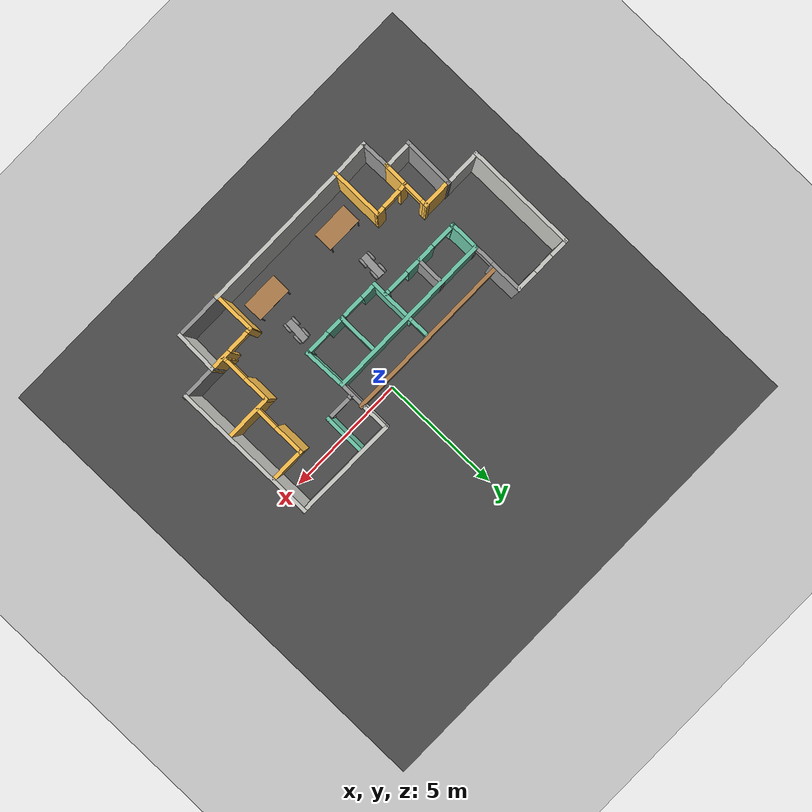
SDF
<sdf version="1.6">
 <world name="default">
  <plugin name="welcome" filename="libwelcome.so"/>
  <light name="sun" type="directional">
   <pose>0 0 10 0 -0 0</pose>
   <diffuse>0.8 0.8 0.8 1</diffuse>
   <specular>0.2 0.2 0.2 1</specular>
   <attenuation>
    <range>1000</range>
    <constant>0.9</constant>
    <linear>0.01</linear>
    <quadratic>0.001</quadratic>
   </attenuation>
   <direction>-0.5 0.1 -0.9</direction>
  </light>
  <model name="ground_plane">
   <static>1</static>
   <link name="link">
    <collision name="collision">
     <geometry><plane><normal>0 0 1</normal><size>100 100</size></plane></geometry>
     <surface>
      <contact><collide_bitmask>65535</collide_bitmask></contact>
      <friction><ode><mu>100</mu><mu2>50</mu2></ode></friction>
     </surface>
    </collision>
    <visual name="visual">
     <cast_shadows>0</cast_shadows>
     <geometry><plane><normal>0 0 1</normal><size>100 100</size></plane></geometry>
     <material>
      <script><uri>file://media/materials/scripts/gazebo.material</uri><name>Gazebo/Grey</name></script>
     </material>
    </visual>
   </link>
  </model>
  <gravity>0 0 -9.8</gravity>
  <magnetic_field>6e-06 2.3e-05 -4.2e-05</magnetic_field>
  <atmosphere type="adiabatic"/>
  <physics name="default_physics" default="0" type="ode">
   <max_step_size>0.001</max_step_size>
   <real_time_factor>1</real_time_factor>
   <real_time_update_rate>1000</real_time_update_rate>
  </physics>
  <scene><ambient>0.4 0.4 0.4 1</ambient><background>0.7 0.7 0.7 1</background><shadows>1</shadows></scene>
  <spherical_coordinates>
   <surface_model>EARTH_WGS84</surface_model>
   <latitude_deg>0</latitude_deg>
   <longitude_deg>0</longitude_deg>
   <elevation>0</elevation>
   <heading_deg>0</heading_deg>
  </spherical_coordinates>
  <model name="building">
   <pose>-1.31872 -2.90365 0 0 -0 0</pose>
   <link name="Wall_14">
    <collision name="Wall_14_Collision">
     <geometry><box><size>6.75 0.15 2.5</size></box></geometry>
     <pose>0 0 1.25 0 -0 0</pose>
    </collision>
    <visual name="Wall_14_Visual">
     <pose>0 0 1.25 0 -0 0</pose>
     <geometry><box><size>6.75 0.15 2.5</size></box></geometry>
     <material>
      <script><uri>file://media/materials/scripts/gazebo.material</uri><name>Gazebo/Wood</name></script>
      <ambient>1 1 1 1</ambient>
     </material>
     <meta><layer>0</layer></meta>
    </visual>
    <pose>-0.771279 2.58365 0 0 -0 3.14159</pose>
   </link>
   <link name="Wall_31">
    <collision name="Wall_31_Collision">
     <geometry><box><size>1.25 0.15 2.5</size></box></geometry>
     <pose>0 0 1.25 0 -0 0</pose>
    </collision>
    <visual name="Wall_31_Visual">
     <pose>0 0 1.25 0 -0 0</pose>
     <geometry><box><size>1.25 0.15 2.5</size></box></geometry>
     <material>
      <script><uri>file://media/materials/scripts/gazebo.material</uri><name>Gazebo/Grey</name></script>
      <ambient>1 0.764706 0.305882 1</ambient>
     </material>
     <meta><layer>0</layer></meta>
    </visual>
    <pose>-4.61808 -0.688752 0 0 -0 0</pose>
   </link>
   <link name="Wall_32">
    <pose>-4.08498 -1.64215 0 0 0 -1.58804</pose>
    <visual name="Wall_32_Visual_0">
     <pose>-0.900343 0 1.25 0 -0 0</pose>
     <geometry><box><size>0.309609 0.15 2.5</size></box></geometry>
     <material>
      <script><uri>file://media/materials/scripts/gazebo.material</uri><name>Gazebo/Grey</name></script>
      <ambient>1 0.764706 0.305882 1</ambient>
     </material>
     <meta><layer>0</layer></meta>
    </visual>
    <collision name="Wall_32_Collision_0">
     <geometry><box><size>0.309609 0.15 2.5</size></box></geometry>
     <pose>-0.900343 0 1.25 0 -0 0</pose>
    </collision>
    <visual name="Wall_32_Visual_1">
     <pose>0.554805 0 1.25 0 -0 0</pose>
     <geometry><box><size>1.00069 0.15 2.5</size></box></geometry>
     <material>
      <script><uri>file://media/materials/scripts/gazebo.material</uri><name>Gazebo/Grey</name></script>
      <ambient>1 0.764706 0.305882 1</ambient>
     </material>
     <meta><layer>0</layer></meta>
    </visual>
    <collision name="Wall_32_Collision_1">
     <geometry><box><size>1.00069 0.15 2.5</size></box></geometry>
     <pose>0.554805 0 1.25 0 -0 0</pose>
    </collision>
    <visual name="Wall_32_Visual_2">
     <pose>-0.345538 0 2.25 0 -0 0</pose>
     <geometry><box><size>0.8 0.15 0.5</size></box></geometry>
     <material>
      <script><uri>file://media/materials/scripts/gazebo.material</uri><name>Gazebo/Grey</name></script>
      <ambient>1 0.764706 0.305882 1</ambient>
     </material>
     <meta><layer>0</layer></meta>
    </visual>
    <collision name="Wall_32_Collision_2">
     <geometry><box><size>0.8 0.15 0.5</size></box></geometry>
     <pose>-0.345538 0 2.25 0 -0 0</pose>
    </collision>
   </link>
   <link name="Wall_34">
    <pose>-3.36907 -1.69258 0 0 -0 0.018781</pose>
    <visual name="Wall_34_Visual_0">
     <pose>-0.59641 0 1.25 0 -0 0</pose>
     <geometry><box><size>0.366972 0.15 2.5</size></box></geometry>
     <material>
      <script><uri>file://media/materials/scripts/gazebo.material</uri><name>Gazebo/Grey</name></script>
      <ambient>1 0.764706 0.305882 1</ambient>
     </material>
     <meta><layer>0</layer></meta>
    </visual>
    <collision name="Wall_34_Collision_0">
     <geometry><box><size>0.366972 0.15 2.5</size></box></geometry>
     <pose>-0.59641 0 1.25 0 -0 0</pose>
    </collision>
    <visual name="Wall_34_Visual_1">
     <pose>0.583486 0 1.25 0 -0 0</pose>
     <geometry><box><size>0.39282 0.15 2.5</size></box></geometry>
     <material>
      <script><uri>file://media/materials/scripts/gazebo.material</uri><name>Gazebo/Grey</name></script>
      <ambient>1 0.764706 0.305882 1</ambient>
     </material>
     <meta><layer>0</layer></meta>
    </visual>
    <collision name="Wall_34_Collision_1">
     <geometry><box><size>0.39282 0.15 2.5</size></box></geometry>
     <pose>0.583486 0 1.25 0 -0 0</pose>
    </collision>
    <visual name="Wall_34_Visual_2">
     <pose>-0.012924 0 2.25 0 -0 0</pose>
     <geometry><box><size>0.8 0.15 0.5</size></box></geometry>
     <material>
      <script><uri>file://media/materials/scripts/gazebo.material</uri><name>Gazebo/Grey</name></script>
      <ambient>1 0.764706 0.305882 1</ambient>
     </material>
     <meta><layer>0</layer></meta>
    </visual>
    <collision name="Wall_34_Collision_2">
     <geometry><box><size>0.8 0.15 0.5</size></box></geometry>
     <pose>-0.012924 0 2.25 0 -0 0</pose>
    </collision>
   </link>
   <link name="Wall_36">
    <collision name="Wall_36_Collision">
     <geometry><box><size>2.13879 0.15 2.5</size></box></geometry>
     <pose>0 0 1.25 0 -0 0</pose>
    </collision>
    <visual name="Wall_36_Visual">
     <pose>0 0 1.25 0 -0 0</pose>
     <geometry><box><size>2.13879 0.15 2.5</size></box></geometry>
     <material>
      <script><uri>file://media/materials/scripts/gazebo.material</uri><name>Gazebo/Grey</name></script>
      <ambient>1 0.764706 0.305882 1</ambient>
     </material>
     <meta><layer>0</layer></meta>
    </visual>
    <pose>-2.66467 -2.70035 0 0 0 -1.5708</pose>
   </link>
   <link name="Wall_37">
    <collision name="Wall_37_Collision">
     <geometry><box><size>1.56095 0.15 2.5</size></box></geometry>
     <pose>0 0 1.25 0 -0 0</pose>
    </collision>
    <visual name="Wall_37_Visual">
     <pose>0 0 1.25 0 -0 0</pose>
     <geometry><box><size>1.56095 0.15 2.5</size></box></geometry>
     <material>
      <script><uri>file://media/materials/scripts/gazebo.material</uri><name>Gazebo/CeilingTiled</name></script>
      <ambient>1 1 1 1</ambient>
     </material>
     <meta><layer>0</layer></meta>
    </visual>
    <pose>-3.36998 -3.69245 0 0 0 -3.10715</pose>
   </link>
   <link name="Wall_38">
    <collision name="Wall_38_Collision">
     <geometry><box><size>1.24492 0.15 2.5</size></box></geometry>
     <pose>0 0 1.25 0 -0 0</pose>
    </collision>
    <visual name="Wall_38_Visual">
     <pose>0 0 1.25 0 -0 0</pose>
     <geometry><box><size>1.24492 0.15 2.5</size></box></geometry>
     <material>
      <script><uri>file://media/materials/scripts/gazebo.material</uri><name>Gazebo/Grey</name></script>
      <ambient>1 1 1 1</ambient>
     </material>
     <meta><layer>0</layer></meta>
    </visual>
    <pose>-4.08858 -3.16945 0 0 -0 1.59509</pose>
   </link>
   <link name="Wall_4">
    <collision name="Wall_4_Collision">
     <geometry><box><size>1.55321 0.15 2.5</size></box></geometry>
     <pose>0 0 1.25 0 -0 0</pose>
    </collision>
    <visual name="Wall_4_Visual">
     <pose>0 0 1.25 0 -0 0</pose>
     <geometry><box><size>1.55321 0.15 2.5</size></box></geometry>
     <material>
      <script><uri>file://media/materials/scripts/gazebo.material</uri><name>Gazebo/CeilingTiled</name></script>
      <ambient>1 1 1 1</ambient>
     </material>
     <meta><layer>0</layer></meta>
    </visual>
    <pose>-5.86968 -0.664749 0 0 -0 0.003702</pose>
   </link>
   <link name="Wall_40">
    <collision name="Wall_40_Collision">
     <geometry><box><size>6.13374 0.15 2.5</size></box></geometry>
     <pose>0 0 1.25 0 -0 0</pose>
    </collision>
    <visual name="Wall_40_Visual">
     <pose>0 0 1.25 0 -0 0</pose>
     <geometry><box><size>6.13374 0.15 2.5</size></box></geometry>
     <material>
      <script><uri>file://media/materials/scripts/gazebo.material</uri><name>Gazebo/CeilingTiled</name></script>
      <ambient>1 1 1 1</ambient>
     </material>
     <meta><layer>0</layer></meta>
    </visual>
    <pose>0.32693 -3.66815 0 0 -0 0</pose>
   </link>
   <link name="Wall_41">
    <collision name="Wall_41_Collision">
     <geometry><box><size>1.75 0.15 2.5</size></box></geometry>
     <pose>0 0 1.25 0 -0 0</pose>
    </collision>
    <visual name="Wall_41_Visual">
     <pose>0 0 1.25 0 -0 0</pose>
     <geometry><box><size>1.75 0.15 2.5</size></box></geometry>
     <material>
      <script><uri>file://media/materials/scripts/gazebo.material</uri><name>Gazebo/Grey</name></script>
      <ambient>1 0.764706 0.305882 1</ambient>
     </material>
     <meta><layer>0</layer></meta>
    </visual>
    <pose>3.29194 -2.89475 0 0 -0 1.5708</pose>
   </link>
   <link name="Wall_43">
    <pose>4.27005 -2.05718 0 0 -0 0.011525</pose>
    <visual name="Wall_43_Visual_0">
     <pose>-0.911062 0 1.25 0 -0 0</pose>
     <geometry><box><size>0.231024 0.15 2.5</size></box></geometry>
     <material>
      <script><uri>file://media/materials/scripts/gazebo.material</uri><name>Gazebo/Grey</name></script>
      <ambient>1 0.764706 0.305882 1</ambient>
     </material>
     <meta><layer>0</layer></meta>
    </visual>
    <collision name="Wall_43_Collision_0">
     <geometry><box><size>0.231024 0.15 2.5</size></box></geometry>
     <pose>-0.911062 0 1.25 0 -0 0</pose>
    </collision>
    <visual name="Wall_43_Visual_1">
     <pose>0.565512 0 1.25 0 -0 0</pose>
     <geometry><box><size>0.922123 0.15 2.5</size></box></geometry>
     <material>
      <script><uri>file://media/materials/scripts/gazebo.material</uri><name>Gazebo/Grey</name></script>
      <ambient>1 0.764706 0.305882 1</ambient>
     </material>
     <meta><layer>0</layer></meta>
    </visual>
    <collision name="Wall_43_Collision_1">
     <geometry><box><size>0.922123 0.15 2.5</size></box></geometry>
     <pose>0.565512 0 1.25 0 -0 0</pose>
    </collision>
    <visual name="Wall_43_Visual_2">
     <pose>-0.34555 0 2.25 0 -0 0</pose>
     <geometry><box><size>0.9 0.15 0.5</size></box></geometry>
     <material>
      <script><uri>file://media/materials/scripts/gazebo.material</uri><name>Gazebo/Grey</name></script>
      <ambient>1 0.764706 0.305882 1</ambient>
     </material>
     <meta><layer>0</layer></meta>
    </visual>
    <collision name="Wall_43_Collision_2">
     <geometry><box><size>0.9 0.15 0.5</size></box></geometry>
     <pose>-0.34555 0 2.25 0 -0 0</pose>
    </collision>
   </link>
   <link name="Wall_44">
    <collision name="Wall_44_Collision">
     <geometry><box><size>1.7728 0.15 2.5</size></box></geometry>
     <pose>0 0 1.25 0 -0 0</pose>
    </collision>
    <visual name="Wall_44_Visual">
     <pose>0 0 1.25 0 -0 0</pose>
     <geometry><box><size>1.7728 0.15 2.5</size></box></geometry>
     <material>
      <script><uri>file://media/materials/scripts/gazebo.material</uri><name>Gazebo/CeilingTiled</name></script>
      <ambient>1 1 1 1</ambient>
     </material>
     <meta><layer>0</layer></meta>
    </visual>
    <pose>5.19505 -2.85718 0 0 0 -1.60347</pose>
   </link>
   <link name="Wall_45">
    <collision name="Wall_45_Collision">
     <geometry><box><size>2 0.15 2.5</size></box></geometry>
     <pose>0 0 1.25 0 -0 0</pose>
    </collision>
    <visual name="Wall_45_Visual">
     <pose>0 0 1.25 0 -0 0</pose>
     <geometry><box><size>2 0.15 2.5</size></box></geometry>
     <material>
      <script><uri>file://media/materials/scripts/gazebo.material</uri><name>Gazebo/Grey</name></script>
      <ambient>1 1 1 1</ambient>
     </material>
     <meta><layer>0</layer></meta>
    </visual>
    <pose>4.24353 -3.66815 0 0 -0 3.14159</pose>
   </link>
   <link name="Wall_47">
    <collision name="Wall_47_Collision">
     <geometry><box><size>1.5 0.15 2.5</size></box></geometry>
     <pose>0 0 1.25 0 -0 0</pose>
    </collision>
    <visual name="Wall_47_Visual">
     <pose>0 0 1.25 0 -0 0</pose>
     <geometry><box><size>1.5 0.15 2.5</size></box></geometry>
     <material>
      <script><uri>file://media/materials/scripts/gazebo.material</uri><name>Gazebo/Grey</name></script>
      <ambient>1 1 1 1</ambient>
     </material>
     <meta><layer>0</layer></meta>
    </visual>
    <pose>5.89656 -2.04621 0 0 -0 0</pose>
   </link>
   <link name="Wall_49">
    <collision name="Wall_49_Collision">
     <geometry><box><size>5.88847 0.15 2.5</size></box></geometry>
     <pose>0 0 1.25 0 -0 0</pose>
    </collision>
    <visual name="Wall_49_Visual">
     <pose>0 0 1.25 0 -0 0</pose>
     <geometry><box><size>5.88847 0.15 2.5</size></box></geometry>
     <material>
      <script><uri>file://media/materials/scripts/gazebo.material</uri><name>Gazebo/CeilingTiled</name></script>
      <ambient>1 1 1 1</ambient>
     </material>
     <meta><layer>0</layer></meta>
    </visual>
    <pose>6.53166 0.822991 0 0 -0 1.57543</pose>
   </link>
   <link name="Wall_5">
    <collision name="Wall_5_Collision">
     <geometry><box><size>2.11029 0.15 2.5</size></box></geometry>
     <pose>0 0 1.25 0 -0 0</pose>
    </collision>
    <visual name="Wall_5_Visual">
     <pose>0 0 1.25 0 -0 0</pose>
     <geometry><box><size>2.11029 0.15 2.5</size></box></geometry>
     <material>
      <script><uri>file://media/materials/scripts/gazebo.material</uri><name>Gazebo/Grey</name></script>
      <ambient>1 1 1 1</ambient>
     </material>
     <meta><layer>0</layer></meta>
    </visual>
    <pose>-5.18498 -1.64215 0 0 0 -1.58804</pose>
   </link>
   <link name="Wall_50">
    <collision name="Wall_50_Collision">
     <geometry><box><size>4.2185 0.15 2.5</size></box></geometry>
     <pose>0 0 1.25 0 -0 0</pose>
    </collision>
    <visual name="Wall_50_Visual">
     <pose>0 0 1.25 0 -0 0</pose>
     <geometry><box><size>4.2185 0.15 2.5</size></box></geometry>
     <material>
      <script><uri>file://media/materials/scripts/gazebo.material</uri><name>Gazebo/CeilingTiled</name></script>
      <ambient>1 1 1 1</ambient>
     </material>
     <meta><layer>0</layer></meta>
    </visual>
    <pose>4.51075 3.70549 0 0 -0 3.13505</pose>
   </link>
   <link name="Wall_51">
    <collision name="Wall_51_Collision">
     <geometry><box><size>1.25 0.15 2.5</size></box></geometry>
     <pose>0 0 1.25 0 -0 0</pose>
    </collision>
    <visual name="Wall_51_Visual">
     <pose>0 0 1.25 0 -0 0</pose>
     <geometry><box><size>1.25 0.15 2.5</size></box></geometry>
     <material>
      <script><uri>file://media/materials/scripts/gazebo.material</uri><name>Gazebo/CeilingTiled</name></script>
      <ambient>1 1 1 1</ambient>
     </material>
     <meta><layer>0</layer></meta>
    </visual>
    <pose>2.47654 3.16879 0 0 0 -1.5708</pose>
   </link>
   <link name="Wall_53">
    <collision name="Wall_53_Collision">
     <geometry><box><size>4.5 0.15 2.5</size></box></geometry>
     <pose>0 0 1.25 0 -0 0</pose>
    </collision>
    <visual name="Wall_53_Visual">
     <pose>0 0 1.25 0 -0 0</pose>
     <geometry><box><size>4.5 0.15 2.5</size></box></geometry>
     <material>
      <script><uri>file://media/materials/scripts/gazebo.material</uri><name>Gazebo/CeilingTiled</name></script>
      <ambient>1 1 1 1</ambient>
     </material>
     <meta><layer>0</layer></meta>
    </visual>
    <pose>-6.57128 1.50765 0 0 -0 1.5708</pose>
   </link>
   <link name="Wall_54">
    <pose>-5.39628 3.68265 0 0 -0 0</pose>
    <visual name="Wall_54_Visual_0">
     <pose>-0.846065 0 1.25 0 -0 0</pose>
     <geometry><box><size>0.807871 0.15 2.5</size></box></geometry>
     <material>
      <script><uri>file://media/materials/scripts/gazebo.material</uri><name>Gazebo/CeilingTiled</name></script>
      <ambient>1 1 1 1</ambient>
     </material>
     <meta><layer>0</layer></meta>
    </visual>
    <collision name="Wall_54_Collision_0">
     <geometry><box><size>0.807871 0.15 2.5</size></box></geometry>
     <pose>-0.846065 0 1.25 0 -0 0</pose>
    </collision>
    <visual name="Wall_54_Visual_1">
     <pose>0.403935 0 0.25 0 -0 0</pose>
     <geometry><box><size>1.69213 0.15 0.5</size></box></geometry>
     <material>
      <script><uri>file://media/materials/scripts/gazebo.material</uri><name>Gazebo/CeilingTiled</name></script>
      <ambient>1 1 1 1</ambient>
     </material>
     <meta><layer>0</layer></meta>
    </visual>
    <collision name="Wall_54_Collision_1">
     <geometry><box><size>1.69213 0.15 0.5</size></box></geometry>
     <pose>0.403935 0 0.25 0 -0 0</pose>
    </collision>
    <visual name="Wall_54_Visual_2">
     <pose>0.803935 0 1.5 0 -0 0</pose>
     <geometry><box><size>0.892129 0.15 2</size></box></geometry>
     <material>
      <script><uri>file://media/materials/scripts/gazebo.material</uri><name>Gazebo/CeilingTiled</name></script>
      <ambient>1 1 1 1</ambient>
     </material>
     <meta><layer>0</layer></meta>
    </visual>
    <collision name="Wall_54_Collision_2">
     <geometry><box><size>0.892129 0.15 2</size></box></geometry>
     <pose>0.803935 0 1.5 0 -0 0</pose>
    </collision>
    <visual name="Wall_54_Visual_3">
     <pose>-0.042129 0 1.9 0 -0 0</pose>
     <geometry><box><size>0.8 0.15 1.2</size></box></geometry>
     <material>
      <script><uri>file://media/materials/scripts/gazebo.material</uri><name>Gazebo/CeilingTiled</name></script>
      <ambient>1 1 1 1</ambient>
     </material>
     <meta><layer>0</layer></meta>
    </visual>
    <collision name="Wall_54_Collision_3">
     <geometry><box><size>0.8 0.15 1.2</size></box></geometry>
     <pose>-0.042129 0 1.9 0 -0 0</pose>
    </collision>
   </link>
   <link name="Wall_56">
    <pose>-4.22128 2.63265 0 0 0 -1.5708</pose>
    <visual name="Wall_56_Visual_0">
     <pose>-0.437256 0 1.25 0 -0 0</pose>
     <geometry><box><size>1.37549 0.15 2.5</size></box></geometry>
     <material>
      <script><uri>file://media/materials/scripts/gazebo.material</uri><name>Gazebo/Grey</name></script>
      <ambient>1 1 1 1</ambient>
     </material>
     <meta><layer>0</layer></meta>
    </visual>
    <collision name="Wall_56_Collision_0">
     <geometry><box><size>1.37549 0.15 2.5</size></box></geometry>
     <pose>-0.437256 0 1.25 0 -0 0</pose>
    </collision>
    <visual name="Wall_56_Visual_1">
     <pose>1.03774 0 1.25 0 -0 0</pose>
     <geometry><box><size>0.174512 0.15 2.5</size></box></geometry>
     <material>
      <script><uri>file://media/materials/scripts/gazebo.material</uri><name>Gazebo/Grey</name></script>
      <ambient>1 1 1 1</ambient>
     </material>
     <meta><layer>0</layer></meta>
    </visual>
    <collision name="Wall_56_Collision_1">
     <geometry><box><size>0.174512 0.15 2.5</size></box></geometry>
     <pose>1.03774 0 1.25 0 -0 0</pose>
    </collision>
    <visual name="Wall_56_Visual_2">
     <pose>0.600488 0 2.25 0 -0 0</pose>
     <geometry><box><size>0.7 0.15 0.5</size></box></geometry>
     <material>
      <script><uri>file://media/materials/scripts/gazebo.material</uri><name>Gazebo/Grey</name></script>
      <ambient>1 1 1 1</ambient>
     </material>
     <meta><layer>0</layer></meta>
    </visual>
    <collision name="Wall_56_Collision_2">
     <geometry><box><size>0.7 0.15 0.5</size></box></geometry>
     <pose>0.600488 0 2.25 0 -0 0</pose>
    </collision>
   </link>
   <link name="Wall_57">
    <collision name="Wall_57_Collision">
     <geometry><box><size>6.84 0.15 2.5</size></box></geometry>
     <pose>0 0 1.25 0 -0 0</pose>
    </collision>
    <visual name="Wall_57_Visual">
     <pose>0 0 1.25 0 -0 0</pose>
     <geometry><box><size>6.84 0.15 2.5</size></box></geometry>
     <material>
      <script><uri>file://media/materials/scripts/gazebo.material</uri><name>Gazebo/Grey</name></script>
      <ambient>0.435294 0.796078 0.67451 1</ambient>
     </material>
     <meta><layer>0</layer></meta>
    </visual>
    <pose>-0.876279 1.58265 0 0 -0 0</pose>
   </link>
   <link name="Wall_58">
    <collision name="Wall_58_Collision">
     <geometry><box><size>1.18617 0.15 2.5</size></box></geometry>
     <pose>0 0 1.25 0 -0 0</pose>
    </collision>
    <visual name="Wall_58_Visual">
     <pose>0 0 1.25 0 -0 0</pose>
     <geometry><box><size>1.18617 0.15 2.5</size></box></geometry>
     <material>
      <script><uri>file://media/materials/scripts/gazebo.material</uri><name>Gazebo/Grey</name></script>
      <ambient>1 1 1 1</ambient>
     </material>
     <meta><layer>0</layer></meta>
    </visual>
    <pose>2.47263 2.10072 0 0 -0 1.56325</pose>
   </link>
   <link name="Wall_6">
    <collision name="Wall_6_Collision">
     <geometry><box><size>1.25 0.15 2.5</size></box></geometry>
     <pose>0 0 1.25 0 -0 0</pose>
    </collision>
    <visual name="Wall_6_Visual">
     <pose>0 0 1.25 0 -0 0</pose>
     <geometry><box><size>1.25 0.15 2.5</size></box></geometry>
     <material>
      <script><uri>file://media/materials/scripts/gazebo.material</uri><name>Gazebo/CeilingTiled</name></script>
      <ambient>1 1 1 1</ambient>
     </material>
     <meta><layer>0</layer></meta>
    </visual>
    <pose>-4.65188 -2.59556 0 0 -0 0</pose>
   </link>
   <link name="Wall_60">
    <pose>-0.836574 1.26417 0 0 0 -1.5708</pose>
    <visual name="Wall_60_Visual_0">
     <pose>-1.2864 0 1.25 0 -0 0</pose>
     <geometry><box><size>0.177203 0.15 2.5</size></box></geometry>
     <material>
      <script><uri>file://media/materials/scripts/gazebo.material</uri><name>Gazebo/Grey</name></script>
      <ambient>0.435294 0.796078 0.67451 1</ambient>
     </material>
     <meta><layer>0</layer></meta>
    </visual>
    <collision name="Wall_60_Collision_0">
     <geometry><box><size>0.177203 0.15 2.5</size></box></geometry>
     <pose>-1.2864 0 1.25 0 -0 0</pose>
    </collision>
    <visual name="Wall_60_Visual_1">
     <pose>0.438602 0 1.25 0 -0 0</pose>
     <geometry><box><size>1.8728 0.15 2.5</size></box></geometry>
     <material>
      <script><uri>file://media/materials/scripts/gazebo.material</uri><name>Gazebo/Grey</name></script>
      <ambient>0.435294 0.796078 0.67451 1</ambient>
     </material>
     <meta><layer>0</layer></meta>
    </visual>
    <collision name="Wall_60_Collision_1">
     <geometry><box><size>1.8728 0.15 2.5</size></box></geometry>
     <pose>0.438602 0 1.25 0 -0 0</pose>
    </collision>
    <visual name="Wall_60_Visual_2">
     <pose>-0.847797 0 2.25 0 -0 0</pose>
     <geometry><box><size>0.7 0.15 0.5</size></box></geometry>
     <material>
      <script><uri>file://media/materials/scripts/gazebo.material</uri><name>Gazebo/Grey</name></script>
      <ambient>0.435294 0.796078 0.67451 1</ambient>
     </material>
     <meta><layer>0</layer></meta>
    </visual>
    <collision name="Wall_60_Collision_2">
     <geometry><box><size>0.7 0.15 0.5</size></box></geometry>
     <pose>-0.847797 0 2.25 0 -0 0</pose>
    </collision>
   </link>
   <link name="Wall_61">
    <pose>0.838426 -0.035831 0 0 -0 0</pose>
    <visual name="Wall_61_Visual_0">
     <pose>-1.3922 0 1.25 0 -0 0</pose>
     <geometry><box><size>0.715608 0.15 2.5</size></box></geometry>
     <material>
      <script><uri>file://media/materials/scripts/gazebo.material</uri><name>Gazebo/Grey</name></script>
      <ambient>0.435294 0.796078 0.67451 1</ambient>
     </material>
     <meta><layer>0</layer></meta>
    </visual>
    <collision name="Wall_61_Collision_0">
     <geometry><box><size>0.715608 0.15 2.5</size></box></geometry>
     <pose>-1.3922 0 1.25 0 -0 0</pose>
    </collision>
    <visual name="Wall_61_Visual_1">
     <pose>0.266815 0 1.25 0 -0 0</pose>
     <geometry><box><size>0.802413 0.15 2.5</size></box></geometry>
     <material>
      <script><uri>file://media/materials/scripts/gazebo.material</uri><name>Gazebo/Grey</name></script>
      <ambient>0.435294 0.796078 0.67451 1</ambient>
     </material>
     <meta><layer>0</layer></meta>
    </visual>
    <collision name="Wall_61_Collision_1">
     <geometry><box><size>0.802413 0.15 2.5</size></box></geometry>
     <pose>0.266815 0 1.25 0 -0 0</pose>
    </collision>
    <visual name="Wall_61_Visual_2">
     <pose>1.65901 0 1.25 0 -0 0</pose>
     <geometry><box><size>0.181979 0.15 2.5</size></box></geometry>
     <material>
      <script><uri>file://media/materials/scripts/gazebo.material</uri><name>Gazebo/Grey</name></script>
      <ambient>0.435294 0.796078 0.67451 1</ambient>
     </material>
     <meta><layer>0</layer></meta>
    </visual>
    <collision name="Wall_61_Collision_2">
     <geometry><box><size>0.181979 0.15 2.5</size></box></geometry>
     <pose>1.65901 0 1.25 0 -0 0</pose>
    </collision>
    <visual name="Wall_61_Visual_3">
     <pose>-0.584392 0 2.25 0 -0 0</pose>
     <geometry><box><size>0.9 0.15 0.5</size></box></geometry>
     <material>
      <script><uri>file://media/materials/scripts/gazebo.material</uri><name>Gazebo/Grey</name></script>
      <ambient>0.435294 0.796078 0.67451 1</ambient>
     </material>
     <meta><layer>0</layer></meta>
    </visual>
    <collision name="Wall_61_Collision_3">
     <geometry><box><size>0.9 0.15 0.5</size></box></geometry>
     <pose>-0.584392 0 2.25 0 -0 0</pose>
    </collision>
    <visual name="Wall_61_Visual_4">
     <pose>1.11802 0 2.25 0 -0 0</pose>
     <geometry><box><size>0.9 0.15 0.5</size></box></geometry>
     <material>
      <script><uri>file://media/materials/scripts/gazebo.material</uri><name>Gazebo/Grey</name></script>
      <ambient>0.435294 0.796078 0.67451 1</ambient>
     </material>
     <meta><layer>0</layer></meta>
    </visual>
    <collision name="Wall_61_Collision_4">
     <geometry><box><size>0.9 0.15 0.5</size></box></geometry>
     <pose>1.11802 0 2.25 0 -0 0</pose>
    </collision>
   </link>
   <link name="Wall_62">
    <collision name="Wall_62_Collision">
     <geometry><box><size>1.7691 0.15 2.5</size></box></geometry>
     <pose>0 0 1.25 0 -0 0</pose>
    </collision>
    <visual name="Wall_62_Visual">
     <pose>0 0 1.25 0 -0 0</pose>
     <geometry><box><size>1.7691 0.15 2.5</size></box></geometry>
     <material>
      <script><uri>file://media/materials/scripts/gazebo.material</uri><name>Gazebo/Grey</name></script>
      <ambient>0.435294 0.796078 0.67451 1</ambient>
     </material>
     <meta><layer>0</layer></meta>
    </visual>
    <pose>2.49107 0.773411 0 0 -0 1.59841</pose>
   </link>
   <link name="Wall_64">
    <collision name="Wall_64_Collision">
     <geometry><box><size>1.75 0.15 2.5</size></box></geometry>
     <pose>0 0 1.25 0 -0 0</pose>
    </collision>
    <visual name="Wall_64_Visual">
     <pose>0 0 1.25 0 -0 0</pose>
     <geometry><box><size>1.75 0.15 2.5</size></box></geometry>
     <material>
      <script><uri>file://media/materials/scripts/gazebo.material</uri><name>Gazebo/Grey</name></script>
      <ambient>0.435294 0.796078 0.67451 1</ambient>
     </material>
     <meta><layer>0</layer></meta>
    </visual>
    <pose>0.812638 0.779962 0 0 0 -1.5708</pose>
   </link>
   <link name="Wall_66">
    <pose>4.66967 -1.01426 0 0 -0 1.5708</pose>
    <visual name="Wall_66_Visual_0">
     <pose>-1.0066 0 1.25 0 -0 0</pose>
     <geometry><box><size>0.236805 0.15 2.5</size></box></geometry>
     <material>
      <script><uri>file://media/materials/scripts/gazebo.material</uri><name>Gazebo/Grey</name></script>
      <ambient>1 0.764706 0.305882 1</ambient>
     </material>
     <meta><layer>0</layer></meta>
    </visual>
    <collision name="Wall_66_Collision_0">
     <geometry><box><size>0.236805 0.15 2.5</size></box></geometry>
     <pose>-1.0066 0 1.25 0 -0 0</pose>
    </collision>
    <visual name="Wall_66_Visual_1">
     <pose>0.568402 0 1.25 0 -0 0</pose>
     <geometry><box><size>1.11319 0.15 2.5</size></box></geometry>
     <material>
      <script><uri>file://media/materials/scripts/gazebo.material</uri><name>Gazebo/Grey</name></script>
      <ambient>1 0.764706 0.305882 1</ambient>
     </material>
     <meta><layer>0</layer></meta>
    </visual>
    <collision name="Wall_66_Collision_1">
     <geometry><box><size>1.11319 0.15 2.5</size></box></geometry>
     <pose>0.568402 0 1.25 0 -0 0</pose>
    </collision>
    <visual name="Wall_66_Visual_2">
     <pose>-0.438195 0 2.25 0 -0 0</pose>
     <geometry><box><size>0.9 0.15 0.5</size></box></geometry>
     <material>
      <script><uri>file://media/materials/scripts/gazebo.material</uri><name>Gazebo/Grey</name></script>
      <ambient>1 0.764706 0.305882 1</ambient>
     </material>
     <meta><layer>0</layer></meta>
    </visual>
    <collision name="Wall_66_Collision_2">
     <geometry><box><size>0.9 0.15 0.5</size></box></geometry>
     <pose>-0.438195 0 2.25 0 -0 0</pose>
    </collision>
   </link>
   <link name="Wall_67">
    <collision name="Wall_67_Collision">
     <geometry><box><size>2 0.15 2.5</size></box></geometry>
     <pose>0 0 1.25 0 -0 0</pose>
    </collision>
    <visual name="Wall_67_Visual">
     <pose>0 0 1.25 0 -0 0</pose>
     <geometry><box><size>2 0.15 2.5</size></box></geometry>
     <material>
      <script><uri>file://media/materials/scripts/gazebo.material</uri><name>Gazebo/Grey</name></script>
      <ambient>1 0.764706 0.305882 1</ambient>
     </material>
     <meta><layer>0</layer></meta>
    </visual>
    <pose>5.59467 0.035735 0 0 -0 0</pose>
   </link>
   <link name="Wall_69">
    <pose>5.14847 1.11375 0 0 -0 1.5708</pose>
    <visual name="Wall_69_Visual_0">
     <pose>-1.0864 0 1.25 0 -0 0</pose>
     <geometry><box><size>0.077203 0.15 2.5</size></box></geometry>
     <material>
      <script><uri>file://media/materials/scripts/gazebo.material</uri><name>Gazebo/Grey</name></script>
      <ambient>1 0.764706 0.305882 1</ambient>
     </material>
     <meta><layer>0</layer></meta>
    </visual>
    <collision name="Wall_69_Collision_0">
     <geometry><box><size>0.077203 0.15 2.5</size></box></geometry>
     <pose>-1.0864 0 1.25 0 -0 0</pose>
    </collision>
    <visual name="Wall_69_Visual_1">
     <pose>0.488602 0 1.25 0 -0 0</pose>
     <geometry><box><size>1.2728 0.15 2.5</size></box></geometry>
     <material>
      <script><uri>file://media/materials/scripts/gazebo.material</uri><name>Gazebo/Grey</name></script>
      <ambient>1 0.764706 0.305882 1</ambient>
     </material>
     <meta><layer>0</layer></meta>
    </visual>
    <collision name="Wall_69_Collision_1">
     <geometry><box><size>1.2728 0.15 2.5</size></box></geometry>
     <pose>0.488602 0 1.25 0 -0 0</pose>
    </collision>
    <visual name="Wall_69_Visual_2">
     <pose>-0.597797 0 2.25 0 -0 0</pose>
     <geometry><box><size>0.9 0.15 0.5</size></box></geometry>
     <material>
      <script><uri>file://media/materials/scripts/gazebo.material</uri><name>Gazebo/Grey</name></script>
      <ambient>1 0.764706 0.305882 1</ambient>
     </material>
     <meta><layer>0</layer></meta>
    </visual>
    <collision name="Wall_69_Collision_2">
     <geometry><box><size>0.9 0.15 0.5</size></box></geometry>
     <pose>-0.597797 0 2.25 0 -0 0</pose>
    </collision>
   </link>
   <link name="Wall_70">
    <collision name="Wall_70_Collision">
     <geometry><box><size>1.5 0.15 2.5</size></box></geometry>
     <pose>0 0 1.25 0 -0 0</pose>
    </collision>
    <visual name="Wall_70_Visual">
     <pose>0 0 1.25 0 -0 0</pose>
     <geometry><box><size>1.5 0.15 2.5</size></box></geometry>
     <material>
      <script><uri>file://media/materials/scripts/gazebo.material</uri><name>Gazebo/Grey</name></script>
      <ambient>1 0.764706 0.305882 1</ambient>
     </material>
     <meta><layer>0</layer></meta>
    </visual>
    <pose>5.82347 2.16375 0 0 -0 0</pose>
   </link>
   <link name="Wall_72">
    <collision name="Wall_72_Collision">
     <geometry><box><size>1.25 0.15 2.5</size></box></geometry>
     <pose>0 0 1.25 0 -0 0</pose>
    </collision>
    <visual name="Wall_72_Visual">
     <pose>0 0 1.25 0 -0 0</pose>
     <geometry><box><size>1.25 0.15 2.5</size></box></geometry>
     <material>
      <script><uri>file://media/materials/scripts/gazebo.material</uri><name>Gazebo/Grey</name></script>
      <ambient>0.435294 0.796078 0.67451 1</ambient>
     </material>
     <meta><layer>0</layer></meta>
    </visual>
    <pose>-4.22128 1.03265 0 0 0 -1.5708</pose>
   </link>
   <link name="Wall_73">
    <pose>-2.54628 0.482654 0 0 -0 0</pose>
    <visual name="Wall_73_Visual_0">
     <pose>-1.65496 0 1.25 0 -0 0</pose>
     <geometry><box><size>0.190084 0.15 2.5</size></box></geometry>
     <material>
      <script><uri>file://media/materials/scripts/gazebo.material</uri><name>Gazebo/Grey</name></script>
      <ambient>0.435294 0.796078 0.67451 1</ambient>
     </material>
     <meta><layer>0</layer></meta>
    </visual>
    <collision name="Wall_73_Collision_0">
     <geometry><box><size>0.190084 0.15 2.5</size></box></geometry>
     <pose>-1.65496 0 1.25 0 -0 0</pose>
    </collision>
    <visual name="Wall_73_Visual_1">
     <pose>-0.019308 0 1.25 0 -0 0</pose>
     <geometry><box><size>1.28122 0.15 2.5</size></box></geometry>
     <material>
      <script><uri>file://media/materials/scripts/gazebo.material</uri><name>Gazebo/Grey</name></script>
      <ambient>0.435294 0.796078 0.67451 1</ambient>
     </material>
     <meta><layer>0</layer></meta>
    </visual>
    <collision name="Wall_73_Collision_1">
     <geometry><box><size>1.28122 0.15 2.5</size></box></geometry>
     <pose>-0.019308 0 1.25 0 -0 0</pose>
    </collision>
    <visual name="Wall_73_Visual_2">
     <pose>1.63565 0 1.25 0 -0 0</pose>
     <geometry><box><size>0.228699 0.15 2.5</size></box></geometry>
     <material>
      <script><uri>file://media/materials/scripts/gazebo.material</uri><name>Gazebo/Grey</name></script>
      <ambient>0.435294 0.796078 0.67451 1</ambient>
     </material>
     <meta><layer>0</layer></meta>
    </visual>
    <collision name="Wall_73_Collision_2">
     <geometry><box><size>0.228699 0.15 2.5</size></box></geometry>
     <pose>1.63565 0 1.25 0 -0 0</pose>
    </collision>
    <visual name="Wall_73_Visual_3">
     <pose>-1.10992 0 2.25 0 -0 0</pose>
     <geometry><box><size>0.9 0.15 0.5</size></box></geometry>
     <material>
      <script><uri>file://media/materials/scripts/gazebo.material</uri><name>Gazebo/Grey</name></script>
      <ambient>0.435294 0.796078 0.67451 1</ambient>
     </material>
     <meta><layer>0</layer></meta>
    </visual>
    <collision name="Wall_73_Collision_3">
     <geometry><box><size>0.9 0.15 0.5</size></box></geometry>
     <pose>-1.10992 0 2.25 0 -0 0</pose>
    </collision>
    <visual name="Wall_73_Visual_4">
     <pose>1.0713 0 2.25 0 -0 0</pose>
     <geometry><box><size>0.9 0.15 0.5</size></box></geometry>
     <material>
      <script><uri>file://media/materials/scripts/gazebo.material</uri><name>Gazebo/Grey</name></script>
      <ambient>0.435294 0.796078 0.67451 1</ambient>
     </material>
     <meta><layer>0</layer></meta>
    </visual>
    <collision name="Wall_73_Collision_4">
     <geometry><box><size>0.9 0.15 0.5</size></box></geometry>
     <pose>1.0713 0 2.25 0 -0 0</pose>
    </collision>
   </link>
   <link name="Wall_75">
    <collision name="Wall_75_Collision">
     <geometry><box><size>1.25 0.15 2.5</size></box></geometry>
     <pose>0 0 1.25 0 -0 0</pose>
    </collision>
    <visual name="Wall_75_Visual">
     <pose>0 0 1.25 0 -0 0</pose>
     <geometry><box><size>1.25 0.15 2.5</size></box></geometry>
     <material>
      <script><uri>file://media/materials/scripts/gazebo.material</uri><name>Gazebo/Grey</name></script>
      <ambient>1 1 1 1</ambient>
     </material>
     <meta><layer>0</layer></meta>
    </visual>
    <pose>-2.51239 1.05656 0 0 0 -1.5708</pose>
   </link>
   <link name="Wall_77">
    <collision name="Wall_77_Collision">
     <geometry><box><size>1.75 0.15 2.5</size></box></geometry>
     <pose>0 0 1.25 0 -0 0</pose>
    </collision>
    <visual name="Wall_77_Visual">
     <pose>0 0 1.25 0 -0 0</pose>
     <geometry><box><size>1.75 0.15 2.5</size></box></geometry>
     <material>
      <script><uri>file://media/materials/scripts/gazebo.material</uri><name>Gazebo/Grey</name></script>
      <ambient>0.435294 0.796078 0.67451 1</ambient>
     </material>
     <meta><layer>0</layer></meta>
    </visual>
    <pose>3.65886 2.88138 0 0 0 -1.5708</pose>
   </link>
   <link name="Wall_78">
    <pose>3.10886 2.08138 0 0 -0 3.14159</pose>
    <visual name="Wall_78_Visual_0">
     <pose>-0.533198 0 1.25 0 -0 0</pose>
     <geometry><box><size>0.183604 0.15 2.5</size></box></geometry>
     <material>
      <script><uri>file://media/materials/scripts/gazebo.material</uri><name>Gazebo/Grey</name></script>
      <ambient>1 1 1 1</ambient>
     </material>
     <meta><layer>0</layer></meta>
    </visual>
    <collision name="Wall_78_Collision_0">
     <geometry><box><size>0.183604 0.15 2.5</size></box></geometry>
     <pose>-0.533198 0 1.25 0 -0 0</pose>
    </collision>
    <visual name="Wall_78_Visual_1">
     <pose>0.541802 0 1.25 0 -0 0</pose>
     <geometry><box><size>0.166396 0.15 2.5</size></box></geometry>
     <material>
      <script><uri>file://media/materials/scripts/gazebo.material</uri><name>Gazebo/Grey</name></script>
      <ambient>1 1 1 1</ambient>
     </material>
     <meta><layer>0</layer></meta>
    </visual>
    <collision name="Wall_78_Collision_1">
     <geometry><box><size>0.166396 0.15 2.5</size></box></geometry>
     <pose>0.541802 0 1.25 0 -0 0</pose>
    </collision>
    <visual name="Wall_78_Visual_2">
     <pose>0.008604 0 2.25 0 -0 0</pose>
     <geometry><box><size>0.9 0.15 0.5</size></box></geometry>
     <material>
      <script><uri>file://media/materials/scripts/gazebo.material</uri><name>Gazebo/Grey</name></script>
      <ambient>1 1 1 1</ambient>
     </material>
     <meta><layer>0</layer></meta>
    </visual>
    <collision name="Wall_78_Collision_2">
     <geometry><box><size>0.9 0.15 0.5</size></box></geometry>
     <pose>0.008604 0 2.25 0 -0 0</pose>
    </collision>
   </link>
   <static>1</static>
  </model>
  <model name="table">
   <static>1</static>
   <link name="link">
    <collision name="surface">
     <pose>0 0 1 0 -0 0</pose>
     <geometry><box><size>1.5 0.8 0.03</size></box></geometry>
     <surface><friction><ode><mu>0.6</mu><mu2>0.6</mu2></ode></friction></surface>
    </collision>
    <visual name="visual1">
     <pose>0 0 1 0 -0 0</pose>
     <geometry><box><size>1.5 0.8 0.03</size></box></geometry>
     <material>
      <script><uri>file://media/materials/scripts/gazebo.material</uri><name>Gazebo/Wood</name></script>
     </material>
    </visual>
    <collision name="front_left_leg">
     <pose>0.68 0.38 0.5 0 -0 0</pose>
     <geometry><cylinder><radius>0.02</radius><length>1</length></cylinder></geometry>
    </collision>
    <visual name="front_left_leg">
     <pose>0.68 0.38 0.5 0 -0 0</pose>
     <geometry><cylinder><radius>0.02</radius><length>1</length></cylinder></geometry>
     <material>
      <script><uri>file://media/materials/scripts/gazebo.material</uri><name>Gazebo/Grey</name></script>
     </material>
    </visual>
    <collision name="front_right_leg">
     <pose>0.68 -0.38 0.5 0 -0 0</pose>
     <geometry><cylinder><radius>0.02</radius><length>1</length></cylinder></geometry>
    </collision>
    <visual name="front_right_leg">
     <pose>0.68 -0.38 0.5 0 -0 0</pose>
     <geometry><cylinder><radius>0.02</radius><length>1</length></cylinder></geometry>
     <material>
      <script><uri>file://media/materials/scripts/gazebo.material</uri><name>Gazebo/Grey</name></script>
     </material>
    </visual>
    <collision name="back_right_leg">
     <pose>-0.68 -0.38 0.5 0 -0 0</pose>
     <geometry><cylinder><radius>0.02</radius><length>1</length></cylinder></geometry>
    </collision>
    <visual name="back_right_leg">
     <pose>-0.68 -0.38 0.5 0 -0 0</pose>
     <geometry><cylinder><radius>0.02</radius><length>1</length></cylinder></geometry>
     <material>
      <script><uri>file://media/materials/scripts/gazebo.material</uri><name>Gazebo/Grey</name></script>
     </material>
    </visual>
    <collision name="back_left_leg">
     <pose>-0.68 0.38 0.5 0 -0 0</pose>
     <geometry><cylinder><radius>0.02</radius><length>1</length></cylinder></geometry>
    </collision>
    <visual name="back_left_leg">
     <pose>-0.68 0.38 0.5 0 -0 0</pose>
     <geometry><cylinder><radius>0.02</radius><length>1</length></cylinder></geometry>
     <material>
      <script><uri>file://media/materials/scripts/gazebo.material</uri><name>Gazebo/Grey</name></script>
     </material>
    </visual>
   </link>
   <pose>-2.76438 -5.48135 0 0 -0 0</pose>
  </model>
  <model name="table_0">
   <static>1</static>
   <link name="link">
    <collision name="surface">
     <pose>0 0 1 0 -0 0</pose>
     <geometry><box><size>1.5 0.8 0.03</size></box></geometry>
     <surface><friction><ode><mu>0.6</mu><mu2>0.6</mu2></ode></friction></surface>
    </collision>
    <visual name="visual1">
     <pose>0 0 1 0 -0 0</pose>
     <geometry><box><size>1.5 0.8 0.03</size></box></geometry>
     <material>
      <script><uri>file://media/materials/scripts/gazebo.material</uri><name>Gazebo/Wood</name></script>
     </material>
    </visual>
    <collision name="front_left_leg">
     <pose>0.68 0.38 0.5 0 -0 0</pose>
     <geometry><cylinder><radius>0.02</radius><length>1</length></cylinder></geometry>
    </collision>
    <visual name="front_left_leg">
     <pose>0.68 0.38 0.5 0 -0 0</pose>
     <geometry><cylinder><radius>0.02</radius><length>1</length></cylinder></geometry>
     <material>
      <script><uri>file://media/materials/scripts/gazebo.material</uri><name>Gazebo/Grey</name></script>
     </material>
    </visual>
    <collision name="front_right_leg">
     <pose>0.68 -0.38 0.5 0 -0 0</pose>
     <geometry><cylinder><radius>0.02</radius><length>1</length></cylinder></geometry>
    </collision>
    <visual name="front_right_leg">
     <pose>0.68 -0.38 0.5 0 -0 0</pose>
     <geometry><cylinder><radius>0.02</radius><length>1</length></cylinder></geometry>
     <material>
      <script><uri>file://media/materials/scripts/gazebo.material</uri><name>Gazebo/Grey</name></script>
     </material>
    </visual>
    <collision name="back_right_leg">
     <pose>-0.68 -0.38 0.5 0 -0 0</pose>
     <geometry><cylinder><radius>0.02</radius><length>1</length></cylinder></geometry>
    </collision>
    <visual name="back_right_leg">
     <pose>-0.68 -0.38 0.5 0 -0 0</pose>
     <geometry><cylinder><radius>0.02</radius><length>1</length></cylinder></geometry>
     <material>
      <script><uri>file://media/materials/scripts/gazebo.material</uri><name>Gazebo/Grey</name></script>
     </material>
    </visual>
    <collision name="back_left_leg">
     <pose>-0.68 0.38 0.5 0 -0 0</pose>
     <geometry><cylinder><radius>0.02</radius><length>1</length></cylinder></geometry>
    </collision>
    <visual name="back_left_leg">
     <pose>-0.68 0.38 0.5 0 -0 0</pose>
     <geometry><cylinder><radius>0.02</radius><length>1</length></cylinder></geometry>
     <material>
      <script><uri>file://media/materials/scripts/gazebo.material</uri><name>Gazebo/Grey</name></script>
     </material>
    </visual>
   </link>
   <pose>0.83404 -5.53908 0 0 -0 0</pose>
  </model>
  <model name="asphalt_plane">
   <static>1</static>
   <link name="link">
    <collision name="collision"><geometry><box><size>20 20 0.1</size></box></geometry></collision>
    <visual name="visual">
     <cast_shadows>0</cast_shadows>
     <geometry><box><size>20 20 0.1</size></box></geometry>
     <material>
      <script>
       <uri>model://asphalt_plane/materials/scripts</uri>
       <uri>model://asphalt_plane/materials/textures</uri>
       <name>vrc/asphalt</name>
      </script>
     </material>
    </visual>
   </link>
   <pose>-0.025239 0.258261 0 0 -0 0</pose>
  </model>
  <model name="myrobot">
   <link name="link_0">
    <pose>1.89771 0.363402 0 0 -0 0</pose>
    <inertial>
     <mass>1</mass>
     <inertia>
      <ixx>0.166667</ixx>
      <ixy>0</ixy>
      <ixz>0</ixz>
      <iyy>0.166667</iyy>
      <iyz>0</iyz>
      <izz>0.166667</izz>
     </inertia>
     <pose>0 0 0.2 0 -0 0</pose>
    </inertial>
    <visual name="visual">
     <geometry><box><size>0.3 1 0.1</size></box></geometry>
     <material>
      <lighting>1</lighting>
      <script><uri>file://media/materials/scripts/gazebo.material</uri><name>Gazebo/Grey</name></script>
      <shader type="pixel"><normal_map>__default__</normal_map></shader>
      <ambient>0.3 0.3 0.3 1</ambient>
      <diffuse>0.7 0.7 0.7 1</diffuse>
      <specular>0.01 0.01 0.01 1</specular>
      <emissive>0 0 0 1</emissive>
     </material>
    </visual>
    <collision name="collision">
     <geometry><box><size>0.3 1 0.1</size></box></geometry>
     <surface>
      <friction>
       <ode><mu>1</mu><mu2>1</mu2><fdir1>0 0 0</fdir1><slip1>0</slip1><slip2>0</slip2></ode>
       <torsional>
        <coefficient>1</coefficient>
        <patch_radius>0</patch_radius>
        <surface_radius>0</surface_radius>
        <use_patch_radius>1</use_patch_radius>
        <ode><slip>0</slip></ode>
       </torsional>
      </friction>
      <bounce><restitution_coefficient>0</restitution_coefficient><threshold>1e+06</threshold></bounce>
      <contact>
       <collide_without_contact>0</collide_without_contact>
       <collide_without_contact_bitmask>1</collide_without_contact_bitmask>
       <collide_bitmask>1</collide_bitmask>
       <ode>
        <soft_cfm>0</soft_cfm>
        <soft_erp>0.2</soft_erp>
        <kp>1e+13</kp>
        <kd>1</kd>
        <max_vel>0.01</max_vel>
        <min_depth>0</min_depth>
       </ode>
       <bullet>
        <split_impulse>1</split_impulse>
        <split_impulse_penetration_threshold>-0.01</split_impulse_penetration_threshold>
        <soft_cfm>0</soft_cfm>
        <soft_erp>0.2</soft_erp>
        <kp>1e+13</kp>
        <kd>1</kd>
       </bullet>
      </contact>
     </surface>
    </collision>
   </link>
   <link name="link_1_clone_clone_0">
    <pose>1.69765 -0.136569 0.1 4.8e-05 1.5707 1.57075</pose>
    <inertial>
     <mass>1</mass>
     <inertia><ixx>0.145833</ixx><ixy>0</ixy><ixz>0</ixz><iyy>0.145833</iyy><iyz>0</iyz><izz>0.125</izz></inertia>
     <pose>0 0 0.2 -0 1.5707 1.5707</pose>
    </inertial>
    <visual name="visual">
     <pose>0 0 0.2 1.5707 -0 0</pose>
     <geometry><cylinder><radius>0.2</radius><length>0.1</length></cylinder></geometry>
     <material>
      <lighting>1</lighting>
      <script><uri>file://media/materials/scripts/gazebo.material</uri><name>Gazebo/Grey</name></script>
      <shader type="pixel"><normal_map>__default__</normal_map></shader>
      <ambient>0.3 0.3 0.3 1</ambient>
      <diffuse>0.7 0.7 0.7 1</diffuse>
      <specular>0.01 0.01 0.01 1</specular>
      <emissive>0 0 0 1</emissive>
     </material>
    </visual>
    <collision name="collision">
     <pose>0 0 0.2 1.5707 -0 0</pose>
     <geometry><cylinder><radius>0.2</radius><length>0.1</length></cylinder></geometry>
     <surface>
      <friction>
       <ode><mu>1</mu><mu2>1</mu2><fdir1>0 0 0</fdir1><slip1>0</slip1><slip2>0</slip2></ode>
       <torsional>
        <coefficient>1</coefficient>
        <patch_radius>0</patch_radius>
        <surface_radius>0</surface_radius>
        <use_patch_radius>1</use_patch_radius>
        <ode><slip>0</slip></ode>
       </torsional>
      </friction>
      <bounce><restitution_coefficient>0</restitution_coefficient><threshold>1e+06</threshold></bounce>
      <contact>
       <collide_without_contact>0</collide_without_contact>
       <collide_without_contact_bitmask>1</collide_without_contact_bitmask>
       <collide_bitmask>1</collide_bitmask>
       <ode>
        <soft_cfm>0</soft_cfm>
        <soft_erp>0.2</soft_erp>
        <kp>1e+13</kp>
        <kd>1</kd>
        <max_vel>0.01</max_vel>
        <min_depth>0</min_depth>
       </ode>
       <bullet>
        <split_impulse>1</split_impulse>
        <split_impulse_penetration_threshold>-0.01</split_impulse_penetration_threshold>
        <soft_cfm>0</soft_cfm>
        <soft_erp>0.2</soft_erp>
        <kp>1e+13</kp>
        <kd>1</kd>
       </bullet>
      </contact>
     </surface>
    </collision>
   </link>
   <link name="link_1_clone_clone_0_clone">
    <pose>2.09773 -0.136569 0.1 -0.000572 1.5707 1.57013</pose>
    <inertial>
     <mass>1</mass>
     <inertia><ixx>0.145833</ixx><ixy>0</ixy><ixz>0</ixz><iyy>0.145833</iyy><iyz>0</iyz><izz>0.125</izz></inertia>
     <pose>0 0 0.2 -0 1.5707 1.5707</pose>
    </inertial>
    <visual name="visual">
     <pose>0 0 0.2 1.5707 -0 0</pose>
     <geometry><cylinder><radius>0.2</radius><length>0.1</length></cylinder></geometry>
     <material>
      <lighting>1</lighting>
      <script><uri>file://media/materials/scripts/gazebo.material</uri><name>Gazebo/Grey</name></script>
      <shader type="pixel"><normal_map>__default__</normal_map></shader>
      <ambient>0.3 0.3 0.3 1</ambient>
      <diffuse>0.7 0.7 0.7 1</diffuse>
      <specular>0.01 0.01 0.01 1</specular>
      <emissive>0 0 0 1</emissive>
     </material>
    </visual>
    <collision name="collision">
     <pose>0 0 0.2 1.5707 -0 0</pose>
     <geometry><cylinder><radius>0.2</radius><length>0.1</length></cylinder></geometry>
     <surface>
      <friction>
       <ode><mu>1</mu><mu2>1</mu2><fdir1>0 0 0</fdir1><slip1>0</slip1><slip2>0</slip2></ode>
       <torsional>
        <coefficient>1</coefficient>
        <patch_radius>0</patch_radius>
        <surface_radius>0</surface_radius>
        <use_patch_radius>1</use_patch_radius>
        <ode><slip>0</slip></ode>
       </torsional>
      </friction>
      <bounce><restitution_coefficient>0</restitution_coefficient><threshold>1e+06</threshold></bounce>
      <contact>
       <collide_without_contact>0</collide_without_contact>
       <collide_without_contact_bitmask>1</collide_without_contact_bitmask>
       <collide_bitmask>1</collide_bitmask>
       <ode>
        <soft_cfm>0</soft_cfm>
        <soft_erp>0.2</soft_erp>
        <kp>1e+13</kp>
        <kd>1</kd>
        <max_vel>0.01</max_vel>
        <min_depth>0</min_depth>
       </ode>
       <bullet>
        <split_impulse>1</split_impulse>
        <split_impulse_penetration_threshold>-0.01</split_impulse_penetration_threshold>
        <soft_cfm>0</soft_cfm>
        <soft_erp>0.2</soft_erp>
        <kp>1e+13</kp>
        <kd>1</kd>
       </bullet>
      </contact>
     </surface>
    </collision>
   </link>
   <link name="link_1_clone_clone_0_clone_0">
    <pose>2.09773 0.463373 0.1 -0.000572 1.5707 1.57013</pose>
    <inertial>
     <mass>1</mass>
     <inertia><ixx>0.145833</ixx><ixy>0</ixy><ixz>0</ixz><iyy>0.145833</iyy><iyz>0</iyz><izz>0.125</izz></inertia>
     <pose>0 0 0.2 -0 1.5707 1.5707</pose>
    </inertial>
    <visual name="visual">
     <pose>0 0 0.2 1.5707 -0 0</pose>
     <geometry><cylinder><radius>0.2</radius><length>0.1</length></cylinder></geometry>
     <material>
      <lighting>1</lighting>
      <script><uri>file://media/materials/scripts/gazebo.material</uri><name>Gazebo/Grey</name></script>
      <shader type="pixel"><normal_map>__default__</normal_map></shader>
      <ambient>0.3 0.3 0.3 1</ambient>
      <diffuse>0.7 0.7 0.7 1</diffuse>
      <specular>0.01 0.01 0.01 1</specular>
      <emissive>0 0 0 1</emissive>
     </material>
    </visual>
    <collision name="collision">
     <pose>0 0 0.2 1.5707 -0 0</pose>
     <geometry><cylinder><radius>0.2</radius><length>0.1</length></cylinder></geometry>
     <surface>
      <friction>
       <ode><mu>1</mu><mu2>1</mu2><fdir1>0 0 0</fdir1><slip1>0</slip1><slip2>0</slip2></ode>
       <torsional>
        <coefficient>1</coefficient>
        <patch_radius>0</patch_radius>
        <surface_radius>0</surface_radius>
        <use_patch_radius>1</use_patch_radius>
        <ode><slip>0</slip></ode>
       </torsional>
      </friction>
      <bounce><restitution_coefficient>0</restitution_coefficient><threshold>1e+06</threshold></bounce>
      <contact>
       <collide_without_contact>0</collide_without_contact>
       <collide_without_contact_bitmask>1</collide_without_contact_bitmask>
       <collide_bitmask>1</collide_bitmask>
       <ode>
        <soft_cfm>0</soft_cfm>
        <soft_erp>0.2</soft_erp>
        <kp>1e+13</kp>
        <kd>1</kd>
        <max_vel>0.01</max_vel>
        <min_depth>0</min_depth>
       </ode>
       <bullet>
        <split_impulse>1</split_impulse>
        <split_impulse_penetration_threshold>-0.01</split_impulse_penetration_threshold>
        <soft_cfm>0</soft_cfm>
        <soft_erp>0.2</soft_erp>
        <kp>1e+13</kp>
        <kd>1</kd>
       </bullet>
      </contact>
     </surface>
    </collision>
   </link>
   <link name="link_1_clone_clone_0_clone_1">
    <pose>1.69765 0.463373 0.1 -0.000572 1.5707 1.57013</pose>
    <inertial>
     <mass>1</mass>
     <inertia><ixx>0.145833</ixx><ixy>0</ixy><ixz>0</ixz><iyy>0.145833</iyy><iyz>0</iyz><izz>0.125</izz></inertia>
     <pose>0 0 0.2 -0 1.5707 1.5707</pose>
    </inertial>
    <visual name="visual">
     <pose>0 0 0.2 1.5707 -0 0</pose>
     <geometry><cylinder><radius>0.2</radius><length>0.1</length></cylinder></geometry>
     <material>
      <lighting>1</lighting>
      <script><uri>file://media/materials/scripts/gazebo.material</uri><name>Gazebo/Grey</name></script>
      <shader type="pixel"><normal_map>__default__</normal_map></shader>
      <ambient>0.3 0.3 0.3 1</ambient>
      <diffuse>0.7 0.7 0.7 1</diffuse>
      <specular>0.01 0.01 0.01 1</specular>
      <emissive>0 0 0 1</emissive>
     </material>
    </visual>
    <collision name="collision">
     <pose>0 0 0.2 1.5707 -0 0</pose>
     <geometry><cylinder><radius>0.2</radius><length>0.1</length></cylinder></geometry>
     <surface>
      <friction>
       <ode><mu>1</mu><mu2>1</mu2><fdir1>0 0 0</fdir1><slip1>0</slip1><slip2>0</slip2></ode>
       <torsional>
        <coefficient>1</coefficient>
        <patch_radius>0</patch_radius>
        <surface_radius>0</surface_radius>
        <use_patch_radius>1</use_patch_radius>
        <ode><slip>0</slip></ode>
       </torsional>
      </friction>
      <bounce><restitution_coefficient>0</restitution_coefficient><threshold>1e+06</threshold></bounce>
      <contact>
       <collide_without_contact>0</collide_without_contact>
       <collide_without_contact_bitmask>1</collide_without_contact_bitmask>
       <collide_bitmask>1</collide_bitmask>
       <ode>
        <soft_cfm>0</soft_cfm>
        <soft_erp>0.2</soft_erp>
        <kp>1e+13</kp>
        <kd>1</kd>
        <max_vel>0.01</max_vel>
        <min_depth>0</min_depth>
       </ode>
       <bullet>
        <split_impulse>1</split_impulse>
        <split_impulse_penetration_threshold>-0.01</split_impulse_penetration_threshold>
        <soft_cfm>0</soft_cfm>
        <soft_erp>0.2</soft_erp>
        <kp>1e+13</kp>
        <kd>1</kd>
       </bullet>
      </contact>
     </surface>
    </collision>
   </link>
   <joint name="link_0_JOINT_5" type="revolute">
    <parent>link_0</parent>
    <child>link_1_clone_clone_0</child>
    <axis>
     <xyz>0 1 0</xyz>
     <use_parent_model_frame>0</use_parent_model_frame>
     <limit>
      <lower>-1.79769e+308</lower>
      <upper>1.79769e+308</upper>
      <effort>-1</effort>
      <velocity>-1</velocity>
     </limit>
     <dynamics>
      <spring_reference>0</spring_reference>
      <spring_stiffness>0</spring_stiffness>
      <damping>0</damping>
      <friction>0</friction>
     </dynamics>
    </axis>
    <physics>
     <ode><limit><cfm>0</cfm><erp>0.2</erp></limit><suspension><cfm>0</cfm><erp>0.2</erp></suspension></ode>
    </physics>
   </joint>
   <joint name="link_0_JOINT_6" type="revolute">
    <parent>link_0</parent>
    <child>link_1_clone_clone_0_clone</child>
    <axis>
     <xyz>0 1 0</xyz>
     <use_parent_model_frame>0</use_parent_model_frame>
     <limit>
      <lower>-1.79769e+308</lower>
      <upper>1.79769e+308</upper>
      <effort>-1</effort>
      <velocity>-1</velocity>
     </limit>
     <dynamics>
      <spring_reference>0</spring_reference>
      <spring_stiffness>0</spring_stiffness>
      <damping>0</damping>
      <friction>0</friction>
     </dynamics>
    </axis>
    <physics>
     <ode><limit><cfm>0</cfm><erp>0.2</erp></limit><suspension><cfm>0</cfm><erp>0.2</erp></suspension></ode>
    </physics>
   </joint>
   <joint name="link_0_JOINT_8" type="revolute">
    <parent>link_0</parent>
    <child>link_1_clone_clone_0_clone_0</child>
    <axis>
     <xyz>0 1 0</xyz>
     <use_parent_model_frame>0</use_parent_model_frame>
     <limit>
      <lower>-1.79769e+308</lower>
      <upper>1.79769e+308</upper>
      <effort>-1</effort>
      <velocity>-1</velocity>
     </limit>
     <dynamics>
      <spring_reference>0</spring_reference>
      <spring_stiffness>0</spring_stiffness>
      <damping>0</damping>
     </dynamics>
    </axis>
    <physics>
     <ode><limit><cfm>0</cfm><erp>0.2</erp></limit><suspension><cfm>0</cfm><erp>0.2</erp></suspension></ode>
    </physics>
   </joint>
   <joint name="link_0_JOINT_9" type="revolute">
    <parent>link_0</parent>
    <child>link_1_clone_clone_0_clone_1</child>
    <axis>
     <xyz>0 1 0</xyz>
     <use_parent_model_frame>0</use_parent_model_frame>
     <limit>
      <lower>-1.79769e+308</lower>
      <upper>1.79769e+308</upper>
      <effort>-1</effort>
      <velocity>-1</velocity>
     </limit>
     <dynamics>
      <spring_reference>0</spring_reference>
      <spring_stiffness>0</spring_stiffness>
      <damping>0</damping>
     </dynamics>
    </axis>
    <physics>
     <ode><limit><cfm>0</cfm><erp>0.2</erp></limit><suspension><cfm>0</cfm><erp>0.2</erp></suspension></ode>
    </physics>
   </joint>
   <static>0</static>
   <pose>-0.976574 -4.23583 0.134888 0.272242 0 -0.057135</pose>
  </model>
  <model name="myrobot_clone">
   <link name="link_0">
    <pose>1.89771 0.363402 0 0 -0 0</pose>
    <inertial>
     <mass>1</mass>
     <inertia>
      <ixx>0.166667</ixx>
      <ixy>0</ixy>
      <ixz>0</ixz>
      <iyy>0.166667</iyy>
      <iyz>0</iyz>
      <izz>0.166667</izz>
     </inertia>
     <pose>0 0 0.2 0 -0 0</pose>
    </inertial>
    <visual name="visual">
     <geometry><box><size>0.3 1 0.1</size></box></geometry>
     <material>
      <lighting>1</lighting>
      <script><uri>file://media/materials/scripts/gazebo.material</uri><name>Gazebo/Grey</name></script>
      <shader type="pixel"><normal_map>__default__</normal_map></shader>
      <ambient>0.3 0.3 0.3 1</ambient>
      <diffuse>0.7 0.7 0.7 1</diffuse>
      <specular>0.01 0.01 0.01 1</specular>
      <emissive>0 0 0 1</emissive>
     </material>
    </visual>
    <collision name="collision">
     <geometry><box><size>0.3 1 0.1</size></box></geometry>
     <surface>
      <friction>
       <ode><mu>1</mu><mu2>1</mu2><fdir1>0 0 0</fdir1><slip1>0</slip1><slip2>0</slip2></ode>
       <torsional>
        <coefficient>1</coefficient>
        <patch_radius>0</patch_radius>
        <surface_radius>0</surface_radius>
        <use_patch_radius>1</use_patch_radius>
        <ode><slip>0</slip></ode>
       </torsional>
      </friction>
      <bounce><restitution_coefficient>0</restitution_coefficient><threshold>1e+06</threshold></bounce>
      <contact>
       <collide_without_contact>0</collide_without_contact>
       <collide_without_contact_bitmask>1</collide_without_contact_bitmask>
       <collide_bitmask>1</collide_bitmask>
       <ode>
        <soft_cfm>0</soft_cfm>
        <soft_erp>0.2</soft_erp>
        <kp>1e+13</kp>
        <kd>1</kd>
        <max_vel>0.01</max_vel>
        <min_depth>0</min_depth>
       </ode>
       <bullet>
        <split_impulse>1</split_impulse>
        <split_impulse_penetration_threshold>-0.01</split_impulse_penetration_threshold>
        <soft_cfm>0</soft_cfm>
        <soft_erp>0.2</soft_erp>
        <kp>1e+13</kp>
        <kd>1</kd>
       </bullet>
      </contact>
     </surface>
    </collision>
   </link>
   <link name="link_1_clone_clone_0">
    <pose>1.69765 -0.136569 0.1 4.8e-05 1.5707 1.57075</pose>
    <inertial>
     <mass>1</mass>
     <inertia><ixx>0.145833</ixx><ixy>0</ixy><ixz>0</ixz><iyy>0.145833</iyy><iyz>0</iyz><izz>0.125</izz></inertia>
     <pose>0 0 0.2 -0 1.5707 1.5707</pose>
    </inertial>
    <visual name="visual">
     <pose>0 0 0.2 1.5707 -0 0</pose>
     <geometry><cylinder><radius>0.2</radius><length>0.1</length></cylinder></geometry>
     <material>
      <lighting>1</lighting>
      <script><uri>file://media/materials/scripts/gazebo.material</uri><name>Gazebo/Grey</name></script>
      <shader type="pixel"><normal_map>__default__</normal_map></shader>
      <ambient>0.3 0.3 0.3 1</ambient>
      <diffuse>0.7 0.7 0.7 1</diffuse>
      <specular>0.01 0.01 0.01 1</specular>
      <emissive>0 0 0 1</emissive>
     </material>
    </visual>
    <collision name="collision">
     <pose>0 0 0.2 1.5707 -0 0</pose>
     <geometry><cylinder><radius>0.2</radius><length>0.1</length></cylinder></geometry>
     <surface>
      <friction>
       <ode><mu>1</mu><mu2>1</mu2><fdir1>0 0 0</fdir1><slip1>0</slip1><slip2>0</slip2></ode>
       <torsional>
        <coefficient>1</coefficient>
        <patch_radius>0</patch_radius>
        <surface_radius>0</surface_radius>
        <use_patch_radius>1</use_patch_radius>
        <ode><slip>0</slip></ode>
       </torsional>
      </friction>
      <bounce><restitution_coefficient>0</restitution_coefficient><threshold>1e+06</threshold></bounce>
      <contact>
       <collide_without_contact>0</collide_without_contact>
       <collide_without_contact_bitmask>1</collide_without_contact_bitmask>
       <collide_bitmask>1</collide_bitmask>
       <ode>
        <soft_cfm>0</soft_cfm>
        <soft_erp>0.2</soft_erp>
        <kp>1e+13</kp>
        <kd>1</kd>
        <max_vel>0.01</max_vel>
        <min_depth>0</min_depth>
       </ode>
       <bullet>
        <split_impulse>1</split_impulse>
        <split_impulse_penetration_threshold>-0.01</split_impulse_penetration_threshold>
        <soft_cfm>0</soft_cfm>
        <soft_erp>0.2</soft_erp>
        <kp>1e+13</kp>
        <kd>1</kd>
       </bullet>
      </contact>
     </surface>
    </collision>
   </link>
   <link name="link_1_clone_clone_0_clone">
    <pose>2.09773 -0.136569 0.1 -0.000572 1.5707 1.57013</pose>
    <inertial>
     <mass>1</mass>
     <inertia><ixx>0.145833</ixx><ixy>0</ixy><ixz>0</ixz><iyy>0.145833</iyy><iyz>0</iyz><izz>0.125</izz></inertia>
     <pose>0 0 0.2 -0 1.5707 1.5707</pose>
    </inertial>
    <visual name="visual">
     <pose>0 0 0.2 1.5707 -0 0</pose>
     <geometry><cylinder><radius>0.2</radius><length>0.1</length></cylinder></geometry>
     <material>
      <lighting>1</lighting>
      <script><uri>file://media/materials/scripts/gazebo.material</uri><name>Gazebo/Grey</name></script>
      <shader type="pixel"><normal_map>__default__</normal_map></shader>
      <ambient>0.3 0.3 0.3 1</ambient>
      <diffuse>0.7 0.7 0.7 1</diffuse>
      <specular>0.01 0.01 0.01 1</specular>
      <emissive>0 0 0 1</emissive>
     </material>
    </visual>
    <collision name="collision">
     <pose>0 0 0.2 1.5707 -0 0</pose>
     <geometry><cylinder><radius>0.2</radius><length>0.1</length></cylinder></geometry>
     <surface>
      <friction>
       <ode><mu>1</mu><mu2>1</mu2><fdir1>0 0 0</fdir1><slip1>0</slip1><slip2>0</slip2></ode>
       <torsional>
        <coefficient>1</coefficient>
        <patch_radius>0</patch_radius>
        <surface_radius>0</surface_radius>
        <use_patch_radius>1</use_patch_radius>
        <ode><slip>0</slip></ode>
       </torsional>
      </friction>
      <bounce><restitution_coefficient>0</restitution_coefficient><threshold>1e+06</threshold></bounce>
      <contact>
       <collide_without_contact>0</collide_without_contact>
       <collide_without_contact_bitmask>1</collide_without_contact_bitmask>
       <collide_bitmask>1</collide_bitmask>
       <ode>
        <soft_cfm>0</soft_cfm>
        <soft_erp>0.2</soft_erp>
        <kp>1e+13</kp>
        <kd>1</kd>
        <max_vel>0.01</max_vel>
        <min_depth>0</min_depth>
       </ode>
       <bullet>
        <split_impulse>1</split_impulse>
        <split_impulse_penetration_threshold>-0.01</split_impulse_penetration_threshold>
        <soft_cfm>0</soft_cfm>
        <soft_erp>0.2</soft_erp>
        <kp>1e+13</kp>
        <kd>1</kd>
       </bullet>
      </contact>
     </surface>
    </collision>
   </link>
   <link name="link_1_clone_clone_0_clone_0">
    <pose>2.09773 0.463373 0.1 -0.000572 1.5707 1.57013</pose>
    <inertial>
     <mass>1</mass>
     <inertia><ixx>0.145833</ixx><ixy>0</ixy><ixz>0</ixz><iyy>0.145833</iyy><iyz>0</iyz><izz>0.125</izz></inertia>
     <pose>0 0 0.2 -0 1.5707 1.5707</pose>
    </inertial>
    <visual name="visual">
     <pose>0 0 0.2 1.5707 -0 0</pose>
     <geometry><cylinder><radius>0.2</radius><length>0.1</length></cylinder></geometry>
     <material>
      <lighting>1</lighting>
      <script><uri>file://media/materials/scripts/gazebo.material</uri><name>Gazebo/Grey</name></script>
      <shader type="pixel"><normal_map>__default__</normal_map></shader>
      <ambient>0.3 0.3 0.3 1</ambient>
      <diffuse>0.7 0.7 0.7 1</diffuse>
      <specular>0.01 0.01 0.01 1</specular>
      <emissive>0 0 0 1</emissive>
     </material>
    </visual>
    <collision name="collision">
     <pose>0 0 0.2 1.5707 -0 0</pose>
     <geometry><cylinder><radius>0.2</radius><length>0.1</length></cylinder></geometry>
     <surface>
      <friction>
       <ode><mu>1</mu><mu2>1</mu2><fdir1>0 0 0</fdir1><slip1>0</slip1><slip2>0</slip2></ode>
       <torsional>
        <coefficient>1</coefficient>
        <patch_radius>0</patch_radius>
        <surface_radius>0</surface_radius>
        <use_patch_radius>1</use_patch_radius>
        <ode><slip>0</slip></ode>
       </torsional>
      </friction>
      <bounce><restitution_coefficient>0</restitution_coefficient><threshold>1e+06</threshold></bounce>
      <contact>
       <collide_without_contact>0</collide_without_contact>
       <collide_without_contact_bitmask>1</collide_without_contact_bitmask>
       <collide_bitmask>1</collide_bitmask>
       <ode>
        <soft_cfm>0</soft_cfm>
        <soft_erp>0.2</soft_erp>
        <kp>1e+13</kp>
        <kd>1</kd>
        <max_vel>0.01</max_vel>
        <min_depth>0</min_depth>
       </ode>
       <bullet>
        <split_impulse>1</split_impulse>
        <split_impulse_penetration_threshold>-0.01</split_impulse_penetration_threshold>
        <soft_cfm>0</soft_cfm>
        <soft_erp>0.2</soft_erp>
        <kp>1e+13</kp>
        <kd>1</kd>
       </bullet>
      </contact>
     </surface>
    </collision>
   </link>
   <link name="link_1_clone_clone_0_clone_1">
    <pose>1.69765 0.463373 0.1 -0.000572 1.5707 1.57013</pose>
    <inertial>
     <mass>1</mass>
     <inertia><ixx>0.145833</ixx><ixy>0</ixy><ixz>0</ixz><iyy>0.145833</iyy><iyz>0</iyz><izz>0.125</izz></inertia>
     <pose>0 0 0.2 -0 1.5707 1.5707</pose>
    </inertial>
    <visual name="visual">
     <pose>0 0 0.2 1.5707 -0 0</pose>
     <geometry><cylinder><radius>0.2</radius><length>0.1</length></cylinder></geometry>
     <material>
      <lighting>1</lighting>
      <script><uri>file://media/materials/scripts/gazebo.material</uri><name>Gazebo/Grey</name></script>
      <shader type="pixel"><normal_map>__default__</normal_map></shader>
      <ambient>0.3 0.3 0.3 1</ambient>
      <diffuse>0.7 0.7 0.7 1</diffuse>
      <specular>0.01 0.01 0.01 1</specular>
      <emissive>0 0 0 1</emissive>
     </material>
    </visual>
    <collision name="collision">
     <pose>0 0 0.2 1.5707 -0 0</pose>
     <geometry><cylinder><radius>0.2</radius><length>0.1</length></cylinder></geometry>
     <surface>
      <friction>
       <ode><mu>1</mu><mu2>1</mu2><fdir1>0 0 0</fdir1><slip1>0</slip1><slip2>0</slip2></ode>
       <torsional>
        <coefficient>1</coefficient>
        <patch_radius>0</patch_radius>
        <surface_radius>0</surface_radius>
        <use_patch_radius>1</use_patch_radius>
        <ode><slip>0</slip></ode>
       </torsional>
      </friction>
      <bounce><restitution_coefficient>0</restitution_coefficient><threshold>1e+06</threshold></bounce>
      <contact>
       <collide_without_contact>0</collide_without_contact>
       <collide_without_contact_bitmask>1</collide_without_contact_bitmask>
       <collide_bitmask>1</collide_bitmask>
       <ode>
        <soft_cfm>0</soft_cfm>
        <soft_erp>0.2</soft_erp>
        <kp>1e+13</kp>
        <kd>1</kd>
        <max_vel>0.01</max_vel>
        <min_depth>0</min_depth>
       </ode>
       <bullet>
        <split_impulse>1</split_impulse>
        <split_impulse_penetration_threshold>-0.01</split_impulse_penetration_threshold>
        <soft_cfm>0</soft_cfm>
        <soft_erp>0.2</soft_erp>
        <kp>1e+13</kp>
        <kd>1</kd>
       </bullet>
      </contact>
     </surface>
    </collision>
   </link>
   <joint name="link_0_JOINT_5" type="revolute">
    <parent>link_0</parent>
    <child>link_1_clone_clone_0</child>
    <axis>
     <xyz>0 1 0</xyz>
     <use_parent_model_frame>0</use_parent_model_frame>
     <limit>
      <lower>-1.79769e+308</lower>
      <upper>1.79769e+308</upper>
      <effort>-1</effort>
      <velocity>-1</velocity>
     </limit>
     <dynamics>
      <spring_reference>0</spring_reference>
      <spring_stiffness>0</spring_stiffness>
      <damping>0</damping>
      <friction>0</friction>
     </dynamics>
    </axis>
    <physics>
     <ode><limit><cfm>0</cfm><erp>0.2</erp></limit><suspension><cfm>0</cfm><erp>0.2</erp></suspension></ode>
    </physics>
   </joint>
   <joint name="link_0_JOINT_6" type="revolute">
    <parent>link_0</parent>
    <child>link_1_clone_clone_0_clone</child>
    <axis>
     <xyz>0 1 0</xyz>
     <use_parent_model_frame>0</use_parent_model_frame>
     <limit>
      <lower>-1.79769e+308</lower>
      <upper>1.79769e+308</upper>
      <effort>-1</effort>
      <velocity>-1</velocity>
     </limit>
     <dynamics>
      <spring_reference>0</spring_reference>
      <spring_stiffness>0</spring_stiffness>
      <damping>0</damping>
      <friction>0</friction>
     </dynamics>
    </axis>
    <physics>
     <ode><limit><cfm>0</cfm><erp>0.2</erp></limit><suspension><cfm>0</cfm><erp>0.2</erp></suspension></ode>
    </physics>
   </joint>
   <joint name="link_0_JOINT_8" type="revolute">
    <parent>link_0</parent>
    <child>link_1_clone_clone_0_clone_0</child>
    <axis>
     <xyz>0 1 0</xyz>
     <use_parent_model_frame>0</use_parent_model_frame>
     <limit>
      <lower>-1.79769e+308</lower>
      <upper>1.79769e+308</upper>
      <effort>-1</effort>
      <velocity>-1</velocity>
     </limit>
     <dynamics>
      <spring_reference>0</spring_reference>
      <spring_stiffness>0</spring_stiffness>
      <damping>0</damping>
     </dynamics>
    </axis>
    <physics>
     <ode><limit><cfm>0</cfm><erp>0.2</erp></limit><suspension><cfm>0</cfm><erp>0.2</erp></suspension></ode>
    </physics>
   </joint>
   <joint name="link_0_JOINT_9" type="revolute">
    <parent>link_0</parent>
    <child>link_1_clone_clone_0_clone_1</child>
    <axis>
     <xyz>0 1 0</xyz>
     <use_parent_model_frame>0</use_parent_model_frame>
     <limit>
      <lower>-1.79769e+308</lower>
      <upper>1.79769e+308</upper>
      <effort>-1</effort>
      <velocity>-1</velocity>
     </limit>
     <dynamics>
      <spring_reference>0</spring_reference>
      <spring_stiffness>0</spring_stiffness>
      <damping>0</damping>
     </dynamics>
    </axis>
    <physics>
     <ode><limit><cfm>0</cfm><erp>0.2</erp></limit><suspension><cfm>0</cfm><erp>0.2</erp></suspension></ode>
    </physics>
   </joint>
   <static>0</static>
   <pose>-4.65041 -3.94546 0.100037 1e-06 1.8e-05 -0.056027</pose>
  </model>
 </world>
</sdf>
